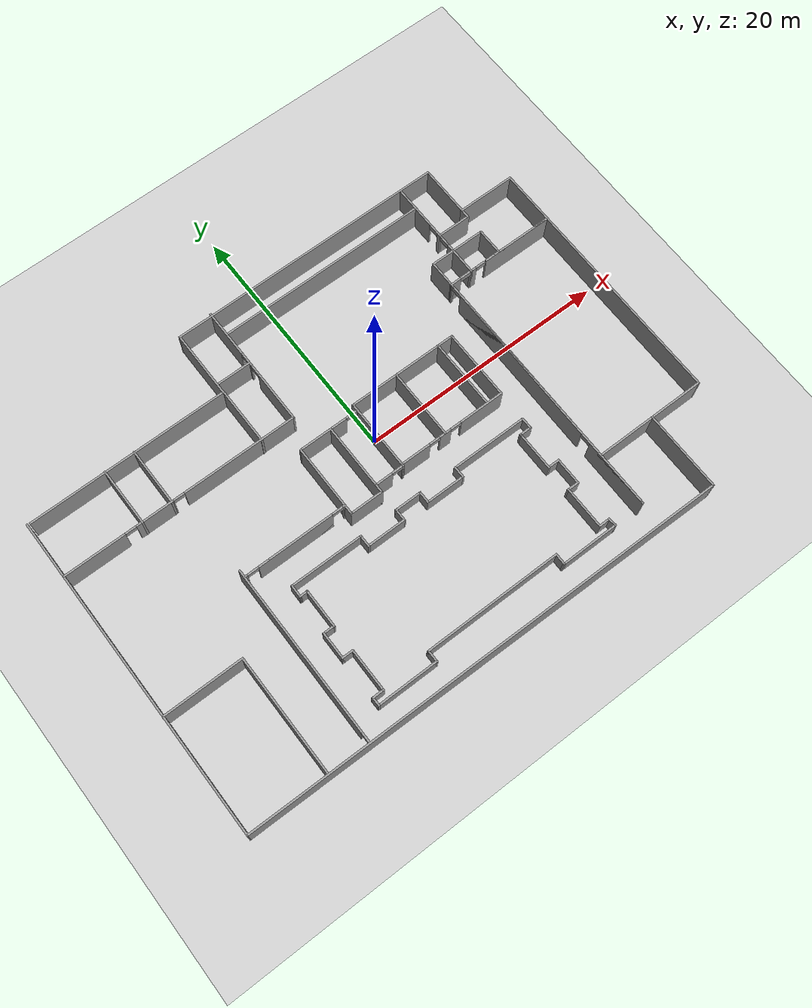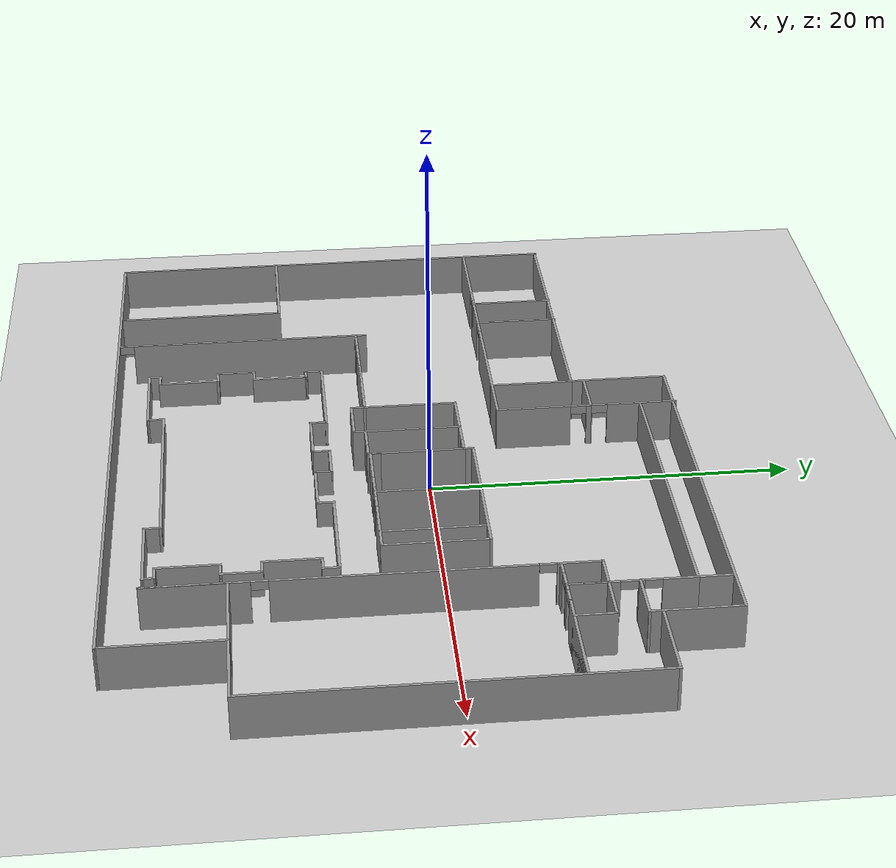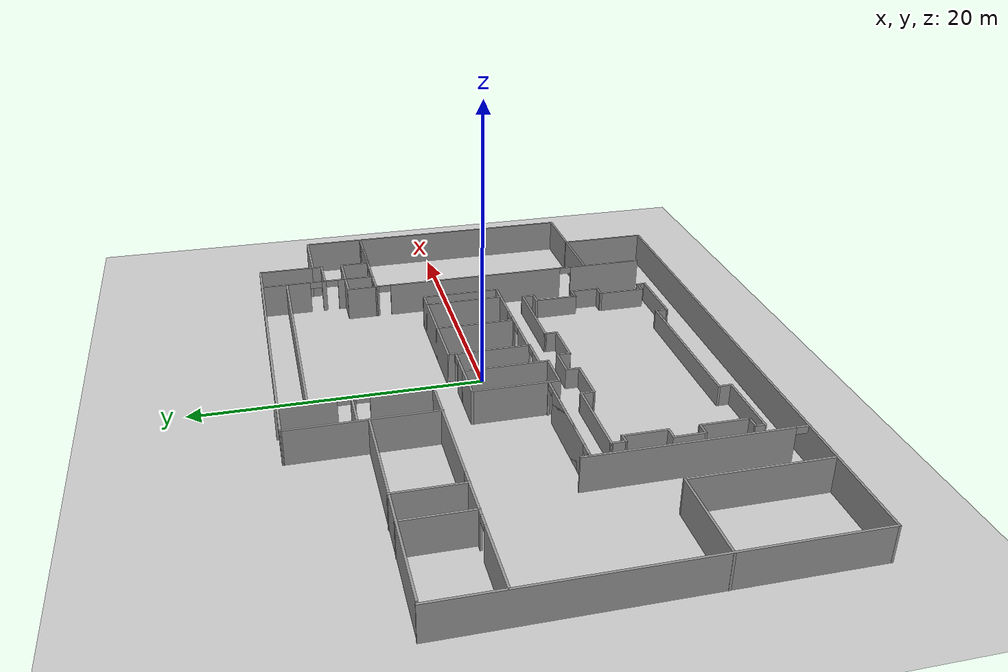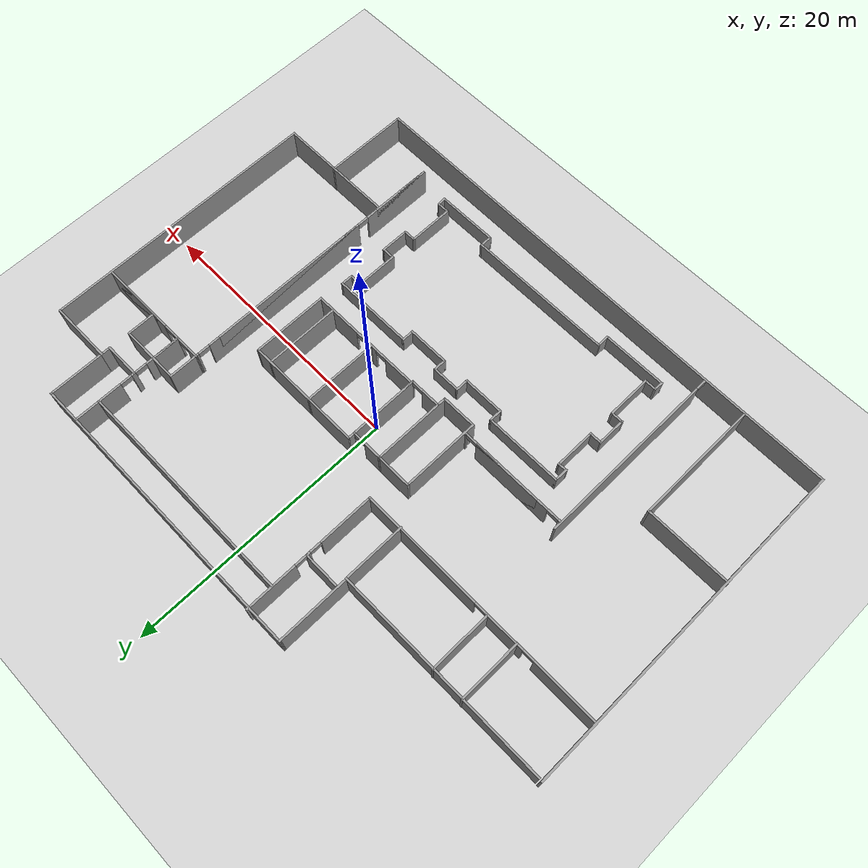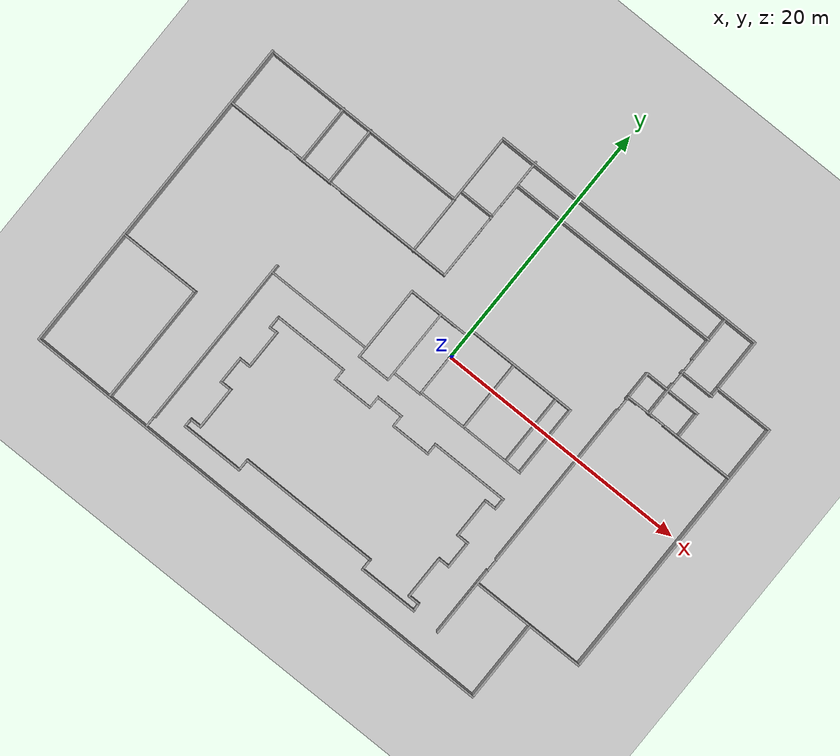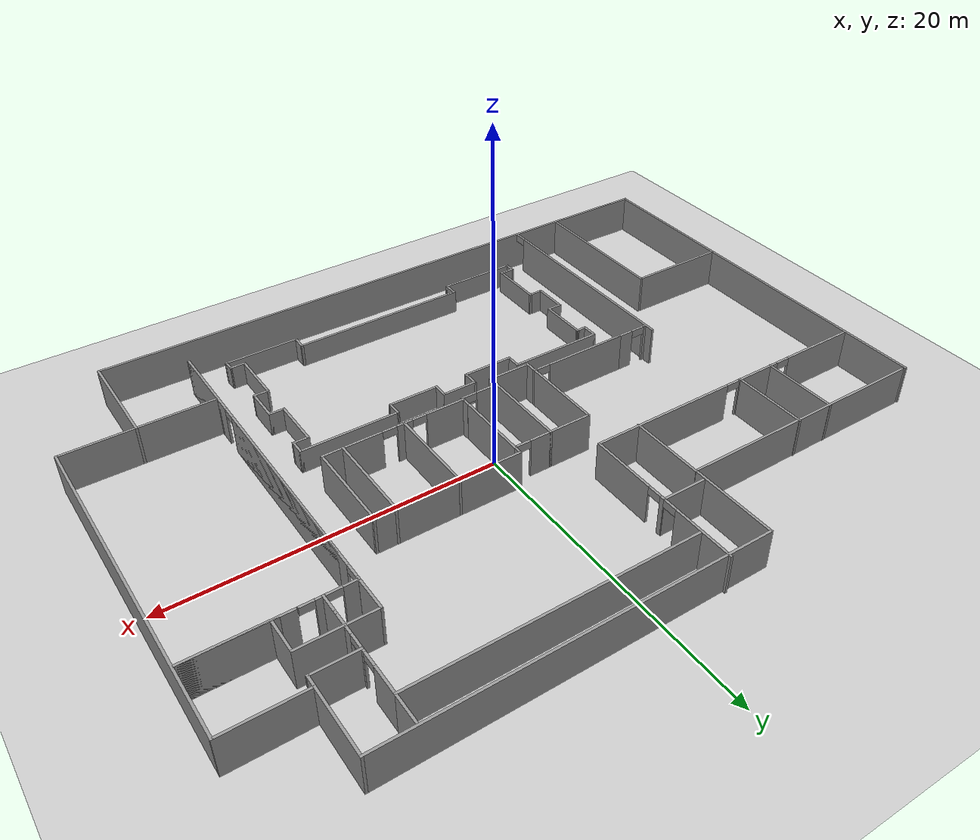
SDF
<sdf version="1.6">
 <world name="default">
  <light name="sun" type="directional">
   <pose>0 0 10 0 -0 0</pose>
   <diffuse>0.8 0.8 0.8 1</diffuse>
   <specular>0.1 0.1 0.1 1</specular>
   <attenuation>
    <range>1000</range>
    <constant>0.9</constant>
    <linear>0.01</linear>
    <quadratic>0.001</quadratic>
   </attenuation>
   <direction>-0.5 0.5 -1</direction>
  </light>
  <model name="ground_plane">
   <static>1</static>
   <link name="link">
    <collision name="collision">
     <geometry><plane><normal>0 0 1</normal><size>100 100</size></plane></geometry>
     <surface><friction><ode><mu>100</mu><mu2>50</mu2></ode></friction></surface>
    </collision>
    <visual name="visual">
     <cast_shadows>0</cast_shadows>
     <geometry><plane><normal>0 0 1</normal><size>100 100</size></plane></geometry>
     <material>
      <script><uri>file://media/materials/scripts/gazebo.material</uri><name>Gazebo/Grey</name></script>
     </material>
    </visual>
   </link>
  </model>
  <gravity>0 0 -9.8</gravity>
  <magnetic_field>6e-06 2.3e-05 -4.2e-05</magnetic_field>
  <atmosphere type="adiabatic"/>
  <physics name="default_physics" default="0" type="ode">
   <max_step_size>0.001</max_step_size>
   <real_time_factor>1</real_time_factor>
   <real_time_update_rate>1000</real_time_update_rate>
  </physics>
  <scene><ambient>0.4 0.4 0.4 1</ambient><background>0.7 0.7 0.7 1</background><shadows>1</shadows></scene>
  <spherical_coordinates>
   <surface_model>EARTH_WGS84</surface_model>
   <latitude_deg>0</latitude_deg>
   <longitude_deg>0</longitude_deg>
   <elevation>0</elevation>
   <heading_deg>0</heading_deg>
  </spherical_coordinates>
  <model name="REPF">
   <pose>-1.32849 -1.57577 0 0 -0 0</pose>
   <link name="Wall_291">
    <collision name="Wall_291_Collision">
     <geometry><box><size>26 0.15 2.5</size></box></geometry>
     <pose>0 0 1.25 0 -0 0</pose>
    </collision>
    <visual name="Wall_291_Visual">
     <pose>0 0 1.25 0 -0 0</pose>
     <geometry><box><size>26 0.15 2.5</size></box></geometry>
     <material>
      <script><uri>file://media/materials/scripts/gazebo.material</uri><name>Gazebo/Grey</name></script>
      <ambient>1 1 1 1</ambient>
     </material>
    </visual>
    <pose>-21.7531 -2.59206 0 0 0 -1.5708</pose>
   </link>
   <link name="Wall_292">
    <collision name="Wall_292_Collision">
     <geometry><box><size>39.3304 0.15 2.5</size></box></geometry>
     <pose>0 0 1.25 0 -0 0</pose>
    </collision>
    <visual name="Wall_292_Visual">
     <pose>0 0 1.25 0 -0 0</pose>
     <geometry><box><size>39.3304 0.15 2.5</size></box></geometry>
     <material>
      <script><uri>file://media/materials/scripts/gazebo.material</uri><name>Gazebo/Grey</name></script>
      <ambient>1 1 1 1</ambient>
     </material>
    </visual>
    <pose>-2.16853 -15.6825 0 0 0 -0.008444</pose>
   </link>
   <link name="Wall_293">
    <collision name="Wall_293_Collision">
     <geometry><box><size>6.5 0.15 2.5</size></box></geometry>
     <pose>0 0 1.25 0 -0 0</pose>
    </collision>
    <visual name="Wall_293_Visual">
     <pose>0 0 1.25 0 -0 0</pose>
     <geometry><box><size>6.5 0.15 2.5</size></box></geometry>
     <material>
      <script><uri>file://media/materials/scripts/gazebo.material</uri><name>Gazebo/Grey</name></script>
      <ambient>1 1 1 1</ambient>
     </material>
    </visual>
    <pose>17.421 -12.6729 0 0 -0 1.5708</pose>
   </link>
   <link name="Wall_294">
    <collision name="Wall_294_Collision">
     <geometry><box><size>4.5 0.15 2.5</size></box></geometry>
     <pose>0 0 1.25 0 -0 0</pose>
    </collision>
    <visual name="Wall_294_Visual">
     <pose>0 0 1.25 0 -0 0</pose>
     <geometry><box><size>4.5 0.15 2.5</size></box></geometry>
     <material>
      <script><uri>file://media/materials/scripts/gazebo.material</uri><name>Gazebo/Grey</name></script>
      <ambient>1 1 1 1</ambient>
     </material>
    </visual>
    <pose>19.596 -9.49791 0 0 -0 0</pose>
   </link>
   <link name="Wall_295">
    <collision name="Wall_295_Collision">
     <geometry><box><size>21.25 0.15 2.5</size></box></geometry>
     <pose>0 0 1.25 0 -0 0</pose>
    </collision>
    <visual name="Wall_295_Visual">
     <pose>0 0 1.25 0 -0 0</pose>
     <geometry><box><size>21.25 0.15 2.5</size></box></geometry>
     <material>
      <script><uri>file://media/materials/scripts/gazebo.material</uri><name>Gazebo/Grey</name></script>
      <ambient>1 1 1 1</ambient>
     </material>
    </visual>
    <pose>21.771 1.05209 0 0 -0 1.5708</pose>
   </link>
   <link name="Wall_296">
    <collision name="Wall_296_Collision">
     <geometry><box><size>4.75 0.15 2.5</size></box></geometry>
     <pose>0 0 1.25 0 -0 0</pose>
    </collision>
    <visual name="Wall_296_Visual">
     <pose>0 0 1.25 0 -0 0</pose>
     <geometry><box><size>4.75 0.15 2.5</size></box></geometry>
     <material>
      <script><uri>file://media/materials/scripts/gazebo.material</uri><name>Gazebo/Grey</name></script>
      <ambient>1 1 1 1</ambient>
     </material>
    </visual>
    <pose>19.471 11.6021 0 0 -0 3.14159</pose>
   </link>
   <link name="Wall_297">
    <collision name="Wall_297_Collision">
     <geometry><box><size>4.25 0.15 2.5</size></box></geometry>
     <pose>0 0 1.25 0 -0 0</pose>
    </collision>
    <visual name="Wall_297_Visual">
     <pose>0 0 1.25 0 -0 0</pose>
     <geometry><box><size>4.25 0.15 2.5</size></box></geometry>
     <material>
      <script><uri>file://media/materials/scripts/gazebo.material</uri><name>Gazebo/Grey</name></script>
      <ambient>1 1 1 1</ambient>
     </material>
    </visual>
    <pose>17.171 13.6521 0 0 -0 1.5708</pose>
   </link>
   <link name="Wall_298">
    <collision name="Wall_298_Collision">
     <geometry><box><size>22.75 0.15 2.5</size></box></geometry>
     <pose>0 0 1.25 0 -0 0</pose>
    </collision>
    <visual name="Wall_298_Visual">
     <pose>0 0 1.25 0 -0 0</pose>
     <geometry><box><size>22.75 0.15 2.5</size></box></geometry>
     <material>
      <script><uri>file://media/materials/scripts/gazebo.material</uri><name>Gazebo/Grey</name></script>
      <ambient>1 1 1 1</ambient>
     </material>
    </visual>
    <pose>5.87097 15.7021 0 0 -0 3.14159</pose>
   </link>
   <link name="Wall_299">
    <collision name="Wall_299_Collision">
     <geometry><box><size>5.55237 0.15 2.5</size></box></geometry>
     <pose>0 0 1.25 0 -0 0</pose>
    </collision>
    <visual name="Wall_299_Visual">
     <pose>0 0 1.25 0 -0 0</pose>
     <geometry><box><size>5.55237 0.15 2.5</size></box></geometry>
     <material>
      <script><uri>file://media/materials/scripts/gazebo.material</uri><name>Gazebo/Grey</name></script>
      <ambient>1 1 1 1</ambient>
     </material>
    </visual>
    <pose>-5.42804 13.0009 0 0 0 -1.57043</pose>
   </link>
   <link name="Wall_300">
    <collision name="Wall_300_Collision">
     <geometry><box><size>16.25 0.15 2.5</size></box></geometry>
     <pose>0 0 1.25 0 -0 0</pose>
    </collision>
    <visual name="Wall_300_Visual">
     <pose>0 0 1.25 0 -0 0</pose>
     <geometry><box><size>16.25 0.15 2.5</size></box></geometry>
     <material>
      <script><uri>file://media/materials/scripts/gazebo.material</uri><name>Gazebo/Grey</name></script>
      <ambient>1 1 1 1</ambient>
     </material>
    </visual>
    <pose>-13.4469 10.2997 0 0 -0 3.14159</pose>
   </link>
   <link name="Wall_302">
    <pose>-2.62455 10.7985 0 0 0 -1.5708</pose>
    <visual name="Wall_302_Visual_0">
     <pose>-3.14213 0 1.25 0 -0 0</pose>
     <geometry><box><size>3.96575 0.15 2.5</size></box></geometry>
     <material>
      <script><uri>file://media/materials/scripts/gazebo.material</uri><name>Gazebo/Grey</name></script>
      <ambient>1 1 1 1</ambient>
     </material>
    </visual>
    <collision name="Wall_302_Collision_0">
     <geometry><box><size>3.96575 0.15 2.5</size></box></geometry>
     <pose>-3.14213 0 1.25 0 -0 0</pose>
    </collision>
    <visual name="Wall_302_Visual_1">
     <pose>-0.118157 0 1.25 0 -0 0</pose>
     <geometry><box><size>0.282192 0.15 2.5</size></box></geometry>
     <material>
      <script><uri>file://media/materials/scripts/gazebo.material</uri><name>Gazebo/Grey</name></script>
      <ambient>1 1 1 1</ambient>
     </material>
    </visual>
    <collision name="Wall_302_Collision_1">
     <geometry><box><size>0.282192 0.15 2.5</size></box></geometry>
     <pose>-0.118157 0 1.25 0 -0 0</pose>
    </collision>
    <visual name="Wall_302_Visual_2">
     <pose>3.02397 0 1.25 0 -0 0</pose>
     <geometry><box><size>4.20206 0.15 2.5</size></box></geometry>
     <material>
      <script><uri>file://media/materials/scripts/gazebo.material</uri><name>Gazebo/Grey</name></script>
      <ambient>1 1 1 1</ambient>
     </material>
    </visual>
    <collision name="Wall_302_Collision_2">
     <geometry><box><size>4.20206 0.15 2.5</size></box></geometry>
     <pose>3.02397 0 1.25 0 -0 0</pose>
    </collision>
    <visual name="Wall_302_Visual_3">
     <pose>-0.709253 0 2.25 0 -0 0</pose>
     <geometry><box><size>0.9 0.15 0.5</size></box></geometry>
     <material>
      <script><uri>file://media/materials/scripts/gazebo.material</uri><name>Gazebo/Grey</name></script>
      <ambient>1 1 1 1</ambient>
     </material>
    </visual>
    <collision name="Wall_302_Collision_3">
     <geometry><box><size>0.9 0.15 0.5</size></box></geometry>
     <pose>-0.709253 0 2.25 0 -0 0</pose>
    </collision>
    <visual name="Wall_302_Visual_4">
     <pose>0.472939 0 2.25 0 -0 0</pose>
     <geometry><box><size>0.9 0.15 0.5</size></box></geometry>
     <material>
      <script><uri>file://media/materials/scripts/gazebo.material</uri><name>Gazebo/Grey</name></script>
      <ambient>1 1 1 1</ambient>
     </material>
    </visual>
    <collision name="Wall_302_Collision_4">
     <geometry><box><size>0.9 0.15 0.5</size></box></geometry>
     <pose>0.472939 0 2.25 0 -0 0</pose>
    </collision>
   </link>
   <link name="Wall_303">
    <pose>-12.1746 5.74854 0 0 -0 3.14159</pose>
    <visual name="Wall_303_Visual_0">
     <pose>-4.94527 0 1.25 0 -0 0</pose>
     <geometry><box><size>9.35946 0.15 2.5</size></box></geometry>
     <material>
      <script><uri>file://media/materials/scripts/gazebo.material</uri><name>Gazebo/Grey</name></script>
      <ambient>1 1 1 1</ambient>
     </material>
    </visual>
    <collision name="Wall_303_Collision_0">
     <geometry><box><size>9.35946 0.15 2.5</size></box></geometry>
     <pose>-4.94527 0 1.25 0 -0 0</pose>
    </collision>
    <visual name="Wall_303_Visual_1">
     <pose>2.17509 0 1.25 0 -0 0</pose>
     <geometry><box><size>3.08126 0.15 2.5</size></box></geometry>
     <material>
      <script><uri>file://media/materials/scripts/gazebo.material</uri><name>Gazebo/Grey</name></script>
      <ambient>1 1 1 1</ambient>
     </material>
    </visual>
    <collision name="Wall_303_Collision_1">
     <geometry><box><size>3.08126 0.15 2.5</size></box></geometry>
     <pose>2.17509 0 1.25 0 -0 0</pose>
    </collision>
    <visual name="Wall_303_Visual_2">
     <pose>7.12036 0 1.25 0 -0 0</pose>
     <geometry><box><size>5.00928 0.15 2.5</size></box></geometry>
     <material>
      <script><uri>file://media/materials/scripts/gazebo.material</uri><name>Gazebo/Grey</name></script>
      <ambient>1 1 1 1</ambient>
     </material>
    </visual>
    <collision name="Wall_303_Collision_2">
     <geometry><box><size>5.00928 0.15 2.5</size></box></geometry>
     <pose>7.12036 0 1.25 0 -0 0</pose>
    </collision>
    <visual name="Wall_303_Visual_3">
     <pose>0.18446 0 2.25 0 -0 0</pose>
     <geometry><box><size>0.9 0.15 0.5</size></box></geometry>
     <material>
      <script><uri>file://media/materials/scripts/gazebo.material</uri><name>Gazebo/Grey</name></script>
      <ambient>1 1 1 1</ambient>
     </material>
    </visual>
    <collision name="Wall_303_Collision_3">
     <geometry><box><size>0.9 0.15 0.5</size></box></geometry>
     <pose>0.18446 0 2.25 0 -0 0</pose>
    </collision>
    <visual name="Wall_303_Visual_4">
     <pose>4.16572 0 2.25 0 -0 0</pose>
     <geometry><box><size>0.9 0.15 0.5</size></box></geometry>
     <material>
      <script><uri>file://media/materials/scripts/gazebo.material</uri><name>Gazebo/Grey</name></script>
      <ambient>1 1 1 1</ambient>
     </material>
    </visual>
    <collision name="Wall_303_Collision_4">
     <geometry><box><size>0.9 0.15 0.5</size></box></geometry>
     <pose>4.16572 0 2.25 0 -0 0</pose>
    </collision>
   </link>
   <link name="Wall_305">
    <collision name="Wall_305_Collision">
     <geometry><box><size>4.75 0.15 2.5</size></box></geometry>
     <pose>0 0 1.25 0 -0 0</pose>
    </collision>
    <visual name="Wall_305_Visual">
     <pose>0 0 1.25 0 -0 0</pose>
     <geometry><box><size>4.75 0.15 2.5</size></box></geometry>
     <material>
      <script><uri>file://media/materials/scripts/gazebo.material</uri><name>Gazebo/Grey</name></script>
      <ambient>1 1 1 1</ambient>
     </material>
    </visual>
    <pose>-5.39685 7.99971 0 0 0 -1.5708</pose>
   </link>
   <link name="Wall_307">
    <collision name="Wall_307_Collision">
     <geometry><box><size>2.75 0.15 2.5</size></box></geometry>
     <pose>0 0 1.25 0 -0 0</pose>
    </collision>
    <visual name="Wall_307_Visual">
     <pose>0 0 1.25 0 -0 0</pose>
     <geometry><box><size>2.75 0.15 2.5</size></box></geometry>
     <material>
      <script><uri>file://media/materials/scripts/gazebo.material</uri><name>Gazebo/Grey</name></script>
      <ambient>1 1 1 1</ambient>
     </material>
    </visual>
    <pose>-3.94634 11.0349 0 0 -0 0</pose>
   </link>
   <link name="Wall_309">
    <collision name="Wall_309_Collision">
     <geometry><box><size>17.25 0.15 2.5</size></box></geometry>
     <pose>0 0 1.25 0 -0 0</pose>
    </collision>
    <visual name="Wall_309_Visual">
     <pose>0 0 1.25 0 -0 0</pose>
     <geometry><box><size>17.25 0.15 2.5</size></box></geometry>
     <material>
      <script><uri>file://media/materials/scripts/gazebo.material</uri><name>Gazebo/Grey</name></script>
      <ambient>1 1 1 1</ambient>
     </material>
    </visual>
    <pose>5.99398 13.832 0 0 -0 0</pose>
   </link>
   <link name="Wall_310">
    <collision name="Wall_310_Collision">
     <geometry><box><size>2 0.15 2.5</size></box></geometry>
     <pose>0 0 1.25 0 -0 0</pose>
    </collision>
    <visual name="Wall_310_Visual">
     <pose>0 0 1.25 0 -0 0</pose>
     <geometry><box><size>2 0.15 2.5</size></box></geometry>
     <material>
      <script><uri>file://media/materials/scripts/gazebo.material</uri><name>Gazebo/Grey</name></script>
      <ambient>1 1 1 1</ambient>
     </material>
    </visual>
    <pose>14.544 14.757 0 0 -0 1.5708</pose>
   </link>
   <link name="Wall_312">
    <pose>14.544 10.532 0 0 0 -1.5708</pose>
    <visual name="Wall_312_Visual_0">
     <pose>-2.44988 0 1.25 0 -0 0</pose>
     <geometry><box><size>1.85025 0.15 2.5</size></box></geometry>
     <material>
      <script><uri>file://media/materials/scripts/gazebo.material</uri><name>Gazebo/Grey</name></script>
      <ambient>1 1 1 1</ambient>
     </material>
    </visual>
    <collision name="Wall_312_Collision_0">
     <geometry><box><size>1.85025 0.15 2.5</size></box></geometry>
     <pose>-2.44988 0 1.25 0 -0 0</pose>
    </collision>
    <visual name="Wall_312_Visual_1">
     <pose>-0.462424 0 1.25 0 -0 0</pose>
     <geometry><box><size>0.324652 0.15 2.5</size></box></geometry>
     <material>
      <script><uri>file://media/materials/scripts/gazebo.material</uri><name>Gazebo/Grey</name></script>
      <ambient>1 1 1 1</ambient>
     </material>
    </visual>
    <collision name="Wall_312_Collision_1">
     <geometry><box><size>0.324652 0.15 2.5</size></box></geometry>
     <pose>-0.462424 0 1.25 0 -0 0</pose>
    </collision>
    <visual name="Wall_312_Visual_2">
     <pose>1.98745 0 1.25 0 -0 0</pose>
     <geometry><box><size>2.7751 0.15 2.5</size></box></geometry>
     <material>
      <script><uri>file://media/materials/scripts/gazebo.material</uri><name>Gazebo/Grey</name></script>
      <ambient>1 1 1 1</ambient>
     </material>
    </visual>
    <collision name="Wall_312_Collision_2">
     <geometry><box><size>2.7751 0.15 2.5</size></box></geometry>
     <pose>1.98745 0 1.25 0 -0 0</pose>
    </collision>
    <visual name="Wall_312_Visual_3">
     <pose>-1.07475 0 2.25 0 -0 0</pose>
     <geometry><box><size>0.9 0.15 0.5</size></box></geometry>
     <material>
      <script><uri>file://media/materials/scripts/gazebo.material</uri><name>Gazebo/Grey</name></script>
      <ambient>1 1 1 1</ambient>
     </material>
    </visual>
    <collision name="Wall_312_Collision_3">
     <geometry><box><size>0.9 0.15 0.5</size></box></geometry>
     <pose>-1.07475 0 2.25 0 -0 0</pose>
    </collision>
    <visual name="Wall_312_Visual_4">
     <pose>0.149902 0 2.25 0 -0 0</pose>
     <geometry><box><size>0.9 0.15 0.5</size></box></geometry>
     <material>
      <script><uri>file://media/materials/scripts/gazebo.material</uri><name>Gazebo/Grey</name></script>
      <ambient>1 1 1 1</ambient>
     </material>
    </visual>
    <collision name="Wall_312_Collision_4">
     <geometry><box><size>0.9 0.15 0.5</size></box></geometry>
     <pose>0.149902 0 2.25 0 -0 0</pose>
    </collision>
   </link>
   <link name="Wall_313">
    <pose>13.619 7.22222 0 0 0 -3.13104</pose>
    <visual name="Wall_313_Visual_0">
     <pose>-0.91553 0 1.25 0 -0 0</pose>
     <geometry><box><size>0.168939 0.15 2.5</size></box></geometry>
     <material>
      <script><uri>file://media/materials/scripts/gazebo.material</uri><name>Gazebo/Grey</name></script>
      <ambient>1 1 1 1</ambient>
     </material>
    </visual>
    <collision name="Wall_313_Collision_0">
     <geometry><box><size>0.168939 0.15 2.5</size></box></geometry>
     <pose>-0.91553 0 1.25 0 -0 0</pose>
    </collision>
    <visual name="Wall_313_Visual_1">
     <pose>0.53447 0 1.25 0 -0 0</pose>
     <geometry><box><size>0.931061 0.15 2.5</size></box></geometry>
     <material>
      <script><uri>file://media/materials/scripts/gazebo.material</uri><name>Gazebo/Grey</name></script>
      <ambient>1 1 1 1</ambient>
     </material>
    </visual>
    <collision name="Wall_313_Collision_1">
     <geometry><box><size>0.931061 0.15 2.5</size></box></geometry>
     <pose>0.53447 0 1.25 0 -0 0</pose>
    </collision>
    <visual name="Wall_313_Visual_2">
     <pose>-0.381061 0 2.25 0 -0 0</pose>
     <geometry><box><size>0.9 0.15 0.5</size></box></geometry>
     <material>
      <script><uri>file://media/materials/scripts/gazebo.material</uri><name>Gazebo/Grey</name></script>
      <ambient>1 1 1 1</ambient>
     </material>
    </visual>
    <collision name="Wall_313_Collision_2">
     <geometry><box><size>0.9 0.15 0.5</size></box></geometry>
     <pose>-0.381061 0 2.25 0 -0 0</pose>
    </collision>
   </link>
   <link name="Wall_314">
    <collision name="Wall_314_Collision">
     <geometry><box><size>2.26953 0.15 2.5</size></box></geometry>
     <pose>0 0 1.25 0 -0 0</pose>
    </collision>
    <visual name="Wall_314_Visual">
     <pose>0 0 1.25 0 -0 0</pose>
     <geometry><box><size>2.26953 0.15 2.5</size></box></geometry>
     <material>
      <script><uri>file://media/materials/scripts/gazebo.material</uri><name>Gazebo/Grey</name></script>
      <ambient>1 1 1 1</ambient>
     </material>
    </visual>
    <pose>12.694 8.27222 0 0 -0 1.5708</pose>
   </link>
   <link name="Wall_315">
    <collision name="Wall_315_Collision">
     <geometry><box><size>2 0.15 2.5</size></box></geometry>
     <pose>0 0 1.25 0 -0 0</pose>
    </collision>
    <visual name="Wall_315_Visual">
     <pose>0 0 1.25 0 -0 0</pose>
     <geometry><box><size>2 0.15 2.5</size></box></geometry>
     <material>
      <script><uri>file://media/materials/scripts/gazebo.material</uri><name>Gazebo/Grey</name></script>
      <ambient>1 1 1 1</ambient>
     </material>
    </visual>
    <pose>13.619 9.33198 0 0 -0 0</pose>
   </link>
   <link name="Wall_317">
    <collision name="Wall_317_Collision">
     <geometry><box><size>2.75 0.15 2.5</size></box></geometry>
     <pose>0 0 1.25 0 -0 0</pose>
    </collision>
    <visual name="Wall_317_Visual">
     <pose>0 0 1.25 0 -0 0</pose>
     <geometry><box><size>2.75 0.15 2.5</size></box></geometry>
     <material>
      <script><uri>file://media/materials/scripts/gazebo.material</uri><name>Gazebo/Grey</name></script>
      <ambient>1 1 1 1</ambient>
     </material>
    </visual>
    <pose>15.8713 10.9244 0 0 -0 0</pose>
   </link>
   <link name="Wall_318">
    <collision name="Wall_318_Collision">
     <geometry><box><size>0.827663 0.15 2.5</size></box></geometry>
     <pose>0 0 1.25 0 -0 0</pose>
    </collision>
    <visual name="Wall_318_Visual">
     <pose>0 0 1.25 0 -0 0</pose>
     <geometry><box><size>0.827663 0.15 2.5</size></box></geometry>
     <material>
      <script><uri>file://media/materials/scripts/gazebo.material</uri><name>Gazebo/Grey</name></script>
      <ambient>1 1 1 1</ambient>
     </material>
    </visual>
    <pose>17.1711 11.2633 0 0 -0 1.57131</pose>
   </link>
   <link name="Wall_320">
    <collision name="Wall_320_Collision">
     <geometry><box><size>2.25 0.15 2.5</size></box></geometry>
     <pose>0 0 1.25 0 -0 0</pose>
    </collision>
    <visual name="Wall_320_Visual">
     <pose>0 0 1.25 0 -0 0</pose>
     <geometry><box><size>2.25 0.15 2.5</size></box></geometry>
     <material>
      <script><uri>file://media/materials/scripts/gazebo.material</uri><name>Gazebo/Grey</name></script>
      <ambient>1 1 1 1</ambient>
     </material>
    </visual>
    <pose>14.544 8.28198 0 0 0 -1.5708</pose>
   </link>
   <link name="Wall_321">
    <pose>18.094 7.23198 0 0 -0 0</pose>
    <visual name="Wall_321_Visual_0">
     <pose>-3.36352 0 1.25 0 -0 0</pose>
     <geometry><box><size>0.522969 0.15 2.5</size></box></geometry>
     <material>
      <script><uri>file://media/materials/scripts/gazebo.material</uri><name>Gazebo/Grey</name></script>
      <ambient>1 1 1 1</ambient>
     </material>
    </visual>
    <collision name="Wall_321_Collision_0">
     <geometry><box><size>0.522969 0.15 2.5</size></box></geometry>
     <pose>-3.36352 0 1.25 0 -0 0</pose>
    </collision>
    <visual name="Wall_321_Visual_1">
     <pose>0.711485 0 1.25 0 -0 0</pose>
     <geometry><box><size>5.82703 0.15 2.5</size></box></geometry>
     <material>
      <script><uri>file://media/materials/scripts/gazebo.material</uri><name>Gazebo/Grey</name></script>
      <ambient>1 1 1 1</ambient>
     </material>
    </visual>
    <collision name="Wall_321_Collision_1">
     <geometry><box><size>5.82703 0.15 2.5</size></box></geometry>
     <pose>0.711485 0 1.25 0 -0 0</pose>
    </collision>
    <visual name="Wall_321_Visual_2">
     <pose>1.13616 0 1.25 0 -0 0</pose>
     <geometry><box><size>4.97768 0.15 2.5</size></box></geometry>
     <material>
      <script><uri>file://media/materials/scripts/gazebo.material</uri><name>Gazebo/Grey</name></script>
      <ambient>1 1 1 1</ambient>
     </material>
    </visual>
    <collision name="Wall_321_Collision_2">
     <geometry><box><size>4.97768 0.15 2.5</size></box></geometry>
     <pose>1.13616 0 1.25 0 -0 0</pose>
    </collision>
    <visual name="Wall_321_Visual_3">
     <pose>-2.67735 0 2.25 0 -0 0</pose>
     <geometry><box><size>0.849354 0.15 0.5</size></box></geometry>
     <material>
      <script><uri>file://media/materials/scripts/gazebo.material</uri><name>Gazebo/Grey</name></script>
      <ambient>1 1 1 1</ambient>
     </material>
    </visual>
    <collision name="Wall_321_Collision_3">
     <geometry><box><size>0.849354 0.15 0.5</size></box></geometry>
     <pose>-2.67735 0 2.25 0 -0 0</pose>
    </collision>
   </link>
   <link name="Wall_323">
    <collision name="Wall_323_Collision">
     <geometry><box><size>2.75 0.15 2.5</size></box></geometry>
     <pose>0 0 1.25 0 -0 0</pose>
    </collision>
    <visual name="Wall_323_Visual">
     <pose>0 0 1.25 0 -0 0</pose>
     <geometry><box><size>2.75 0.15 2.5</size></box></geometry>
     <material>
      <script><uri>file://media/materials/scripts/gazebo.material</uri><name>Gazebo/Grey</name></script>
      <ambient>1 1 1 1</ambient>
     </material>
    </visual>
    <pose>15.844 9.33198 0 0 -0 0</pose>
   </link>
   <link name="Wall_324">
    <collision name="Wall_324_Collision">
     <geometry><box><size>2.25 0.15 2.5</size></box></geometry>
     <pose>0 0 1.25 0 -0 0</pose>
    </collision>
    <visual name="Wall_324_Visual">
     <pose>0 0 1.25 0 -0 0</pose>
     <geometry><box><size>2.25 0.15 2.5</size></box></geometry>
     <material>
      <script><uri>file://media/materials/scripts/gazebo.material</uri><name>Gazebo/Grey</name></script>
      <ambient>1 1 1 1</ambient>
     </material>
    </visual>
    <pose>17.144 8.28198 0 0 0 -1.5708</pose>
   </link>
   <link name="Wall_327">
    <pose>12.694 -3.32778 0 0 0 -1.5708</pose>
    <visual name="Wall_327_Visual_0">
     <pose>-10.4755 0 1.25 0 -0 0</pose>
     <geometry><box><size>0.29897 0.15 2.5</size></box></geometry>
     <material>
      <script><uri>file://media/materials/scripts/gazebo.material</uri><name>Gazebo/Grey</name></script>
      <ambient>1 1 1 1</ambient>
     </material>
    </visual>
    <collision name="Wall_327_Collision_0">
     <geometry><box><size>0.29897 0.15 2.5</size></box></geometry>
     <pose>-10.4755 0 1.25 0 -0 0</pose>
    </collision>
    <visual name="Wall_327_Visual_1">
     <pose>-2.64993 0 1.25 0 -0 0</pose>
     <geometry><box><size>13.5522 0.15 2.5</size></box></geometry>
     <material>
      <script><uri>file://media/materials/scripts/gazebo.material</uri><name>Gazebo/Grey</name></script>
      <ambient>1 1 1 1</ambient>
     </material>
    </visual>
    <collision name="Wall_327_Collision_1">
     <geometry><box><size>13.5522 0.15 2.5</size></box></geometry>
     <pose>-2.64993 0 1.25 0 -0 0</pose>
    </collision>
    <visual name="Wall_327_Visual_2">
     <pose>-2.20373 0 1.25 0 -0 0</pose>
     <geometry><box><size>12.6598 0.15 2.5</size></box></geometry>
     <material>
      <script><uri>file://media/materials/scripts/gazebo.material</uri><name>Gazebo/Grey</name></script>
      <ambient>1 1 1 1</ambient>
     </material>
    </visual>
    <collision name="Wall_327_Collision_2">
     <geometry><box><size>12.6598 0.15 2.5</size></box></geometry>
     <pose>-2.20373 0 1.25 0 -0 0</pose>
    </collision>
    <visual name="Wall_327_Visual_3">
     <pose>7.82559 0 1.25 0 -0 0</pose>
     <geometry><box><size>5.59883 0.15 2.5</size></box></geometry>
     <material>
      <script><uri>file://media/materials/scripts/gazebo.material</uri><name>Gazebo/Grey</name></script>
      <ambient>1 1 1 1</ambient>
     </material>
    </visual>
    <collision name="Wall_327_Collision_3">
     <geometry><box><size>5.59883 0.15 2.5</size></box></geometry>
     <pose>7.82559 0 1.25 0 -0 0</pose>
    </collision>
    <visual name="Wall_327_Visual_4">
     <pose>8.27478 0 1.25 0 -0 0</pose>
     <geometry><box><size>4.70045 0.15 2.5</size></box></geometry>
     <material>
      <script><uri>file://media/materials/scripts/gazebo.material</uri><name>Gazebo/Grey</name></script>
      <ambient>1 1 1 1</ambient>
     </material>
    </visual>
    <collision name="Wall_327_Collision_4">
     <geometry><box><size>4.70045 0.15 2.5</size></box></geometry>
     <pose>8.27478 0 1.25 0 -0 0</pose>
    </collision>
    <visual name="Wall_327_Visual_5">
     <pose>-9.87983 0 2.25 0 -0 0</pose>
     <geometry><box><size>0.892405 0.15 0.5</size></box></geometry>
     <material>
      <script><uri>file://media/materials/scripts/gazebo.material</uri><name>Gazebo/Grey</name></script>
      <ambient>1 1 1 1</ambient>
     </material>
    </visual>
    <collision name="Wall_327_Collision_5">
     <geometry><box><size>0.892405 0.15 0.5</size></box></geometry>
     <pose>-9.87983 0 2.25 0 -0 0</pose>
    </collision>
    <visual name="Wall_327_Visual_6">
     <pose>4.57536 0 2.25 0 -0 0</pose>
     <geometry><box><size>0.89838 0.15 0.5</size></box></geometry>
     <material>
      <script><uri>file://media/materials/scripts/gazebo.material</uri><name>Gazebo/Grey</name></script>
      <ambient>1 1 1 1</ambient>
     </material>
    </visual>
    <collision name="Wall_327_Collision_6">
     <geometry><box><size>0.89838 0.15 0.5</size></box></geometry>
     <pose>4.57536 0 2.25 0 -0 0</pose>
    </collision>
    <visual name="Wall_327_Visual_7">
     <pose>4.57536 0 2.25 0 -0 0</pose>
     <geometry><box><size>0.89838 0.15 0.5</size></box></geometry>
     <material>
      <script><uri>file://media/materials/scripts/gazebo.material</uri><name>Gazebo/Grey</name></script>
      <ambient>1 1 1 1</ambient>
     </material>
    </visual>
    <collision name="Wall_327_Collision_7">
     <geometry><box><size>0.89838 0.15 0.5</size></box></geometry>
     <pose>4.57536 0 2.25 0 -0 0</pose>
    </collision>
   </link>
   <link name="Wall_329">
    <collision name="Wall_329_Collision">
     <geometry><box><size>4.75 0.15 2.5</size></box></geometry>
     <pose>0 0 1.25 0 -0 0</pose>
    </collision>
    <visual name="Wall_329_Visual">
     <pose>0 0 1.25 0 -0 0</pose>
     <geometry><box><size>4.75 0.15 2.5</size></box></geometry>
     <material>
      <script><uri>file://media/materials/scripts/gazebo.material</uri><name>Gazebo/Grey</name></script>
      <ambient>1 1 1 1</ambient>
     </material>
    </visual>
    <pose>15.121 -9.49791 0 0 -0 3.14159</pose>
   </link>
   <link name="Wall_331">
    <collision name="Wall_331_Collision">
     <geometry><box><size>6.5 0.15 2.5</size></box></geometry>
     <pose>0 0 1.25 0 -0 0</pose>
    </collision>
    <visual name="Wall_331_Visual">
     <pose>0 0 1.25 0 -0 0</pose>
     <geometry><box><size>6.5 0.15 2.5</size></box></geometry>
     <material>
      <script><uri>file://media/materials/scripts/gazebo.material</uri><name>Gazebo/Grey</name></script>
      <ambient>1 1 1 1</ambient>
     </material>
    </visual>
    <pose>-18.596 -6.09631 0 0 -0 0</pose>
   </link>
   <link name="Wall_332">
    <collision name="Wall_332_Collision">
     <geometry><box><size>9.5 0.15 2.5</size></box></geometry>
     <pose>0 0 1.25 0 -0 0</pose>
    </collision>
    <visual name="Wall_332_Visual">
     <pose>0 0 1.25 0 -0 0</pose>
     <geometry><box><size>9.5 0.15 2.5</size></box></geometry>
     <material>
      <script><uri>file://media/materials/scripts/gazebo.material</uri><name>Gazebo/Grey</name></script>
      <ambient>1 1 1 1</ambient>
     </material>
    </visual>
    <pose>-15.421 -10.7713 0 0 0 -1.5708</pose>
   </link>
   <link name="Wall_334">
    <pose>-12.1022 -8.27314 0 0 0 -1.5708</pose>
    <visual name="Wall_334_Visual_0">
     <pose>-0.398977 0 1.25 0 -0 0</pose>
     <geometry><box><size>13.702 0.15 2.5</size></box></geometry>
     <material>
      <script><uri>file://media/materials/scripts/gazebo.material</uri><name>Gazebo/Grey</name></script>
      <ambient>1 1 1 1</ambient>
     </material>
    </visual>
    <collision name="Wall_334_Collision_0">
     <geometry><box><size>13.702 0.15 2.5</size></box></geometry>
     <pose>-0.398977 0 1.25 0 -0 0</pose>
    </collision>
    <visual name="Wall_334_Visual_1">
     <pose>6.85102 0 2.25 0 -0 0</pose>
     <geometry><box><size>0.797955 0.15 0.5</size></box></geometry>
     <material>
      <script><uri>file://media/materials/scripts/gazebo.material</uri><name>Gazebo/Grey</name></script>
      <ambient>1 1 1 1</ambient>
     </material>
    </visual>
    <collision name="Wall_334_Collision_1">
     <geometry><box><size>0.797955 0.15 0.5</size></box></geometry>
     <pose>6.85102 0 2.25 0 -0 0</pose>
    </collision>
   </link>
   <link name="Wall_336">
    <pose>-7.83845 -1.65312 0 0 -0 0</pose>
    <visual name="Wall_336_Visual_0">
     <pose>-4.13254 0 1.25 0 -0 0</pose>
     <geometry><box><size>0.234928 0.15 2.5</size></box></geometry>
     <material>
      <script><uri>file://media/materials/scripts/gazebo.material</uri><name>Gazebo/Grey</name></script>
      <ambient>1 1 1 1</ambient>
     </material>
    </visual>
    <collision name="Wall_336_Collision_0">
     <geometry><box><size>0.234928 0.15 2.5</size></box></geometry>
     <pose>-4.13254 0 1.25 0 -0 0</pose>
    </collision>
    <visual name="Wall_336_Visual_1">
     <pose>-0.006322 0 1.25 0 -0 0</pose>
     <geometry><box><size>6.2175 0.15 2.5</size></box></geometry>
     <material>
      <script><uri>file://media/materials/scripts/gazebo.material</uri><name>Gazebo/Grey</name></script>
      <ambient>1 1 1 1</ambient>
     </material>
    </visual>
    <collision name="Wall_336_Collision_1">
     <geometry><box><size>6.2175 0.15 2.5</size></box></geometry>
     <pose>-0.006322 0 1.25 0 -0 0</pose>
    </collision>
    <visual name="Wall_336_Visual_2">
     <pose>0.440485 0 1.25 0 -0 0</pose>
     <geometry><box><size>5.32388 0.15 2.5</size></box></geometry>
     <material>
      <script><uri>file://media/materials/scripts/gazebo.material</uri><name>Gazebo/Grey</name></script>
      <ambient>1 1 1 1</ambient>
     </material>
    </visual>
    <collision name="Wall_336_Collision_2">
     <geometry><box><size>5.32388 0.15 2.5</size></box></geometry>
     <pose>0.440485 0 1.25 0 -0 0</pose>
    </collision>
    <visual name="Wall_336_Visual_3">
     <pose>4.12621 0 1.25 0 -0 0</pose>
     <geometry><box><size>0.247573 0.15 2.5</size></box></geometry>
     <material>
      <script><uri>file://media/materials/scripts/gazebo.material</uri><name>Gazebo/Grey</name></script>
      <ambient>1 1 1 1</ambient>
     </material>
    </visual>
    <collision name="Wall_336_Collision_3">
     <geometry><box><size>0.247573 0.15 2.5</size></box></geometry>
     <pose>4.12621 0 1.25 0 -0 0</pose>
    </collision>
    <visual name="Wall_336_Visual_4">
     <pose>-3.56826 0 2.25 0 -0 0</pose>
     <geometry><box><size>0.893616 0.15 0.5</size></box></geometry>
     <material>
      <script><uri>file://media/materials/scripts/gazebo.material</uri><name>Gazebo/Grey</name></script>
      <ambient>1 1 1 1</ambient>
     </material>
    </visual>
    <collision name="Wall_336_Collision_4">
     <geometry><box><size>0.893616 0.15 0.5</size></box></geometry>
     <pose>-3.56826 0 2.25 0 -0 0</pose>
    </collision>
    <visual name="Wall_336_Visual_5">
     <pose>3.55243 0 2.25 0 -0 0</pose>
     <geometry><box><size>0.9 0.15 0.5</size></box></geometry>
     <material>
      <script><uri>file://media/materials/scripts/gazebo.material</uri><name>Gazebo/Grey</name></script>
      <ambient>1 1 1 1</ambient>
     </material>
    </visual>
    <collision name="Wall_336_Collision_5">
     <geometry><box><size>0.9 0.15 0.5</size></box></geometry>
     <pose>3.55243 0 2.25 0 -0 0</pose>
    </collision>
    <visual name="Wall_336_Visual_6">
     <pose>3.55243 0 2.25 0 -0 0</pose>
     <geometry><box><size>0.9 0.15 0.5</size></box></geometry>
     <material>
      <script><uri>file://media/materials/scripts/gazebo.material</uri><name>Gazebo/Grey</name></script>
      <ambient>1 1 1 1</ambient>
     </material>
    </visual>
    <collision name="Wall_336_Collision_6">
     <geometry><box><size>0.9 0.15 0.5</size></box></geometry>
     <pose>3.55243 0 2.25 0 -0 0</pose>
    </collision>
   </link>
   <link name="Wall_338">
    <collision name="Wall_338_Collision">
     <geometry><box><size>6 0.15 2.5</size></box></geometry>
     <pose>0 0 1.25 0 -0 0</pose>
    </collision>
    <visual name="Wall_338_Visual">
     <pose>0 0 1.25 0 -0 0</pose>
     <geometry><box><size>6 0.15 2.5</size></box></geometry>
     <material>
      <script><uri>file://media/materials/scripts/gazebo.material</uri><name>Gazebo/Grey</name></script>
      <ambient>1 1 1 1</ambient>
     </material>
    </visual>
    <pose>-3.6668 0.527981 0 0 0 -1.5708</pose>
   </link>
   <link name="Wall_339">
    <collision name="Wall_339_Collision">
     <geometry><box><size>2.75 0.15 2.5</size></box></geometry>
     <pose>0 0 1.25 0 -0 0</pose>
    </collision>
    <visual name="Wall_339_Visual">
     <pose>0 0 1.25 0 -0 0</pose>
     <geometry><box><size>2.75 0.15 2.5</size></box></geometry>
     <material>
      <script><uri>file://media/materials/scripts/gazebo.material</uri><name>Gazebo/Grey</name></script>
      <ambient>1 1 1 1</ambient>
     </material>
    </visual>
    <pose>-2.3668 -2.39702 0 0 -0 0</pose>
   </link>
   <link name="Wall_340">
    <collision name="Wall_340_Collision">
     <geometry><box><size>6 0.15 2.5</size></box></geometry>
     <pose>0 0 1.25 0 -0 0</pose>
    </collision>
    <visual name="Wall_340_Visual">
     <pose>0 0 1.25 0 -0 0</pose>
     <geometry><box><size>6 0.15 2.5</size></box></geometry>
     <material>
      <script><uri>file://media/materials/scripts/gazebo.material</uri><name>Gazebo/Grey</name></script>
      <ambient>1 1 1 1</ambient>
     </material>
    </visual>
    <pose>-1.0668 0.527981 0 0 -0 1.5708</pose>
   </link>
   <link name="Wall_341">
    <collision name="Wall_341_Collision">
     <geometry><box><size>2.75 0.15 2.5</size></box></geometry>
     <pose>0 0 1.25 0 -0 0</pose>
    </collision>
    <visual name="Wall_341_Visual">
     <pose>0 0 1.25 0 -0 0</pose>
     <geometry><box><size>2.75 0.15 2.5</size></box></geometry>
     <material>
      <script><uri>file://media/materials/scripts/gazebo.material</uri><name>Gazebo/Grey</name></script>
      <ambient>1 1 1 1</ambient>
     </material>
    </visual>
    <pose>-2.3668 3.45298 0 0 -0 3.14159</pose>
   </link>
   <link name="Wall_343">
    <pose>0.108198 3.45298 0 0 -0 0</pose>
    <visual name="Wall_343_Visual_0">
     <pose>-0.544207 0 1.25 0 -0 0</pose>
     <geometry><box><size>1.41159 0.15 2.5</size></box></geometry>
     <material>
      <script><uri>file://media/materials/scripts/gazebo.material</uri><name>Gazebo/Grey</name></script>
      <ambient>1 1 1 1</ambient>
     </material>
    </visual>
    <collision name="Wall_343_Collision_0">
     <geometry><box><size>1.41159 0.15 2.5</size></box></geometry>
     <pose>-0.544207 0 1.25 0 -0 0</pose>
    </collision>
    <visual name="Wall_343_Visual_1">
     <pose>1.15579 0 1.25 0 -0 0</pose>
     <geometry><box><size>0.188414 0.15 2.5</size></box></geometry>
     <material>
      <script><uri>file://media/materials/scripts/gazebo.material</uri><name>Gazebo/Grey</name></script>
      <ambient>1 1 1 1</ambient>
     </material>
    </visual>
    <collision name="Wall_343_Collision_1">
     <geometry><box><size>0.188414 0.15 2.5</size></box></geometry>
     <pose>1.15579 0 1.25 0 -0 0</pose>
    </collision>
    <visual name="Wall_343_Visual_2">
     <pose>0.611586 0 2.25 0 -0 0</pose>
     <geometry><box><size>0.9 0.15 0.5</size></box></geometry>
     <material>
      <script><uri>file://media/materials/scripts/gazebo.material</uri><name>Gazebo/Grey</name></script>
      <ambient>1 1 1 1</ambient>
     </material>
    </visual>
    <collision name="Wall_343_Collision_2">
     <geometry><box><size>0.9 0.15 0.5</size></box></geometry>
     <pose>0.611586 0 2.25 0 -0 0</pose>
    </collision>
   </link>
   <link name="Wall_344">
    <collision name="Wall_344_Collision">
     <geometry><box><size>5.25 0.15 2.5</size></box></geometry>
     <pose>0 0 1.25 0 -0 0</pose>
    </collision>
    <visual name="Wall_344_Visual">
     <pose>0 0 1.25 0 -0 0</pose>
     <geometry><box><size>5.25 0.15 2.5</size></box></geometry>
     <material>
      <script><uri>file://media/materials/scripts/gazebo.material</uri><name>Gazebo/Grey</name></script>
      <ambient>1 1 1 1</ambient>
     </material>
    </visual>
    <pose>1.2832 0.902981 0 0 0 -1.5708</pose>
   </link>
   <link name="Wall_345">
    <pose>5.7082 -1.64702 0 0 -0 0</pose>
    <visual name="Wall_345_Visual_0">
     <pose>-3.24073 0 1.25 0 -0 0</pose>
     <geometry><box><size>2.51854 0.15 2.5</size></box></geometry>
     <material>
      <script><uri>file://media/materials/scripts/gazebo.material</uri><name>Gazebo/Grey</name></script>
      <ambient>1 1 1 1</ambient>
     </material>
    </visual>
    <collision name="Wall_345_Collision_0">
     <geometry><box><size>2.51854 0.15 2.5</size></box></geometry>
     <pose>-3.24073 0 1.25 0 -0 0</pose>
    </collision>
    <visual name="Wall_345_Visual_1">
     <pose>-0.593536 0 1.25 0 -0 0</pose>
     <geometry><box><size>0.97585 0.15 2.5</size></box></geometry>
     <material>
      <script><uri>file://media/materials/scripts/gazebo.material</uri><name>Gazebo/Grey</name></script>
      <ambient>1 1 1 1</ambient>
     </material>
    </visual>
    <collision name="Wall_345_Collision_1">
     <geometry><box><size>0.97585 0.15 2.5</size></box></geometry>
     <pose>-0.593536 0 1.25 0 -0 0</pose>
    </collision>
    <visual name="Wall_345_Visual_2">
     <pose>2.64719 0 1.25 0 -0 0</pose>
     <geometry><box><size>3.70561 0.15 2.5</size></box></geometry>
     <material>
      <script><uri>file://media/materials/scripts/gazebo.material</uri><name>Gazebo/Grey</name></script>
      <ambient>1 1 1 1</ambient>
     </material>
    </visual>
    <collision name="Wall_345_Collision_2">
     <geometry><box><size>3.70561 0.15 2.5</size></box></geometry>
     <pose>2.64719 0 1.25 0 -0 0</pose>
    </collision>
    <visual name="Wall_345_Visual_3">
     <pose>-1.53146 0 2.25 0 -0 0</pose>
     <geometry><box><size>0.9 0.15 0.5</size></box></geometry>
     <material>
      <script><uri>file://media/materials/scripts/gazebo.material</uri><name>Gazebo/Grey</name></script>
      <ambient>1 1 1 1</ambient>
     </material>
    </visual>
    <collision name="Wall_345_Collision_3">
     <geometry><box><size>0.9 0.15 0.5</size></box></geometry>
     <pose>-1.53146 0 2.25 0 -0 0</pose>
    </collision>
    <visual name="Wall_345_Visual_4">
     <pose>0.344389 0 2.25 0 -0 0</pose>
     <geometry><box><size>0.9 0.15 0.5</size></box></geometry>
     <material>
      <script><uri>file://media/materials/scripts/gazebo.material</uri><name>Gazebo/Grey</name></script>
      <ambient>1 1 1 1</ambient>
     </material>
    </visual>
    <collision name="Wall_345_Collision_4">
     <geometry><box><size>0.9 0.15 0.5</size></box></geometry>
     <pose>0.344389 0 2.25 0 -0 0</pose>
    </collision>
   </link>
   <link name="Wall_346">
    <collision name="Wall_346_Collision">
     <geometry><box><size>5.75 0.15 2.5</size></box></geometry>
     <pose>0 0 1.25 0 -0 0</pose>
    </collision>
    <visual name="Wall_346_Visual">
     <pose>0 0 1.25 0 -0 0</pose>
     <geometry><box><size>5.75 0.15 2.5</size></box></geometry>
     <material>
      <script><uri>file://media/materials/scripts/gazebo.material</uri><name>Gazebo/Grey</name></script>
      <ambient>1 1 1 1</ambient>
     </material>
    </visual>
    <pose>10.1332 1.15298 0 0 -0 1.5708</pose>
   </link>
   <link name="Wall_347">
    <collision name="Wall_347_Collision">
     <geometry><box><size>9 0.15 2.5</size></box></geometry>
     <pose>0 0 1.25 0 -0 0</pose>
    </collision>
    <visual name="Wall_347_Visual">
     <pose>0 0 1.25 0 -0 0</pose>
     <geometry><box><size>9 0.15 2.5</size></box></geometry>
     <material>
      <script><uri>file://media/materials/scripts/gazebo.material</uri><name>Gazebo/Grey</name></script>
      <ambient>1 1 1 1</ambient>
     </material>
    </visual>
    <pose>5.7082 3.95298 0 0 -0 3.14159</pose>
   </link>
   <link name="Wall_349">
    <pose>0.116601 -1.76431 0 0 -0 0</pose>
    <visual name="Wall_349_Visual_0">
     <pose>-0.510841 0 1.25 0 -0 0</pose>
     <geometry><box><size>1.47832 0.15 2.5</size></box></geometry>
     <material>
      <script><uri>file://media/materials/scripts/gazebo.material</uri><name>Gazebo/Grey</name></script>
      <ambient>1 1 1 1</ambient>
     </material>
    </visual>
    <collision name="Wall_349_Collision_0">
     <geometry><box><size>1.47832 0.15 2.5</size></box></geometry>
     <pose>-0.510841 0 1.25 0 -0 0</pose>
    </collision>
    <visual name="Wall_349_Visual_1">
     <pose>1.18916 0 1.25 0 -0 0</pose>
     <geometry><box><size>0.121682 0.15 2.5</size></box></geometry>
     <material>
      <script><uri>file://media/materials/scripts/gazebo.material</uri><name>Gazebo/Grey</name></script>
      <ambient>1 1 1 1</ambient>
     </material>
    </visual>
    <collision name="Wall_349_Collision_1">
     <geometry><box><size>0.121682 0.15 2.5</size></box></geometry>
     <pose>1.18916 0 1.25 0 -0 0</pose>
    </collision>
    <visual name="Wall_349_Visual_2">
     <pose>0.678318 0 2.25 0 -0 0</pose>
     <geometry><box><size>0.9 0.15 0.5</size></box></geometry>
     <material>
      <script><uri>file://media/materials/scripts/gazebo.material</uri><name>Gazebo/Grey</name></script>
      <ambient>1 1 1 1</ambient>
     </material>
    </visual>
    <collision name="Wall_349_Collision_2">
     <geometry><box><size>0.9 0.15 0.5</size></box></geometry>
     <pose>0.678318 0 2.25 0 -0 0</pose>
    </collision>
   </link>
   <link name="Wall_350">
    <collision name="Wall_350_Collision">
     <geometry><box><size>0.75 0.15 2.5</size></box></geometry>
     <pose>0 0 1.25 0 -0 0</pose>
    </collision>
    <visual name="Wall_350_Visual">
     <pose>0 0 1.25 0 -0 0</pose>
     <geometry><box><size>0.75 0.15 2.5</size></box></geometry>
     <material>
      <script><uri>file://media/materials/scripts/gazebo.material</uri><name>Gazebo/Grey</name></script>
      <ambient>1 1 1 1</ambient>
     </material>
    </visual>
    <pose>1.2916 -1.46431 0 0 -0 1.5708</pose>
   </link>
   <link name="Wall_352">
    <collision name="Wall_352_Collision">
     <geometry><box><size>5.75 0.15 2.5</size></box></geometry>
     <pose>0 0 1.25 0 -0 0</pose>
    </collision>
    <visual name="Wall_352_Visual">
     <pose>0 0 1.25 0 -0 0</pose>
     <geometry><box><size>5.75 0.15 2.5</size></box></geometry>
     <material>
      <script><uri>file://media/materials/scripts/gazebo.material</uri><name>Gazebo/Grey</name></script>
      <ambient>1 1 1 1</ambient>
     </material>
    </visual>
    <pose>5.11026 1.15574 0 0 0 -1.5708</pose>
   </link>
   <link name="Wall_354">
    <collision name="Wall_354_Collision">
     <geometry><box><size>4.75 0.15 1.5</size></box></geometry>
     <pose>0 0 0.75 0 -0 0</pose>
    </collision>
    <visual name="Wall_354_Visual">
     <pose>0 0 0.75 0 -0 0</pose>
     <geometry><box><size>4.75 0.15 1.5</size></box></geometry>
     <material>
      <script><uri>file://media/materials/scripts/gazebo.material</uri><name>Gazebo/Grey</name></script>
      <ambient>1 1 1 1</ambient>
     </material>
    </visual>
    <pose>8.2026 -13.8241 0 0 -0 3.14159</pose>
   </link>
   <link name="Wall_355">
    <collision name="Wall_355_Collision">
     <geometry><box><size>1 0.15 1.5</size></box></geometry>
     <pose>0 0 0.75 0 -0 0</pose>
    </collision>
    <visual name="Wall_355_Visual">
     <pose>0 0 0.75 0 -0 0</pose>
     <geometry><box><size>1 0.15 1.5</size></box></geometry>
     <material>
      <script><uri>file://media/materials/scripts/gazebo.material</uri><name>Gazebo/Grey</name></script>
      <ambient>1 1 1 1</ambient>
     </material>
    </visual>
    <pose>5.9026 -13.3991 0 0 -0 1.5708</pose>
   </link>
   <link name="Wall_356">
    <collision name="Wall_356_Collision">
     <geometry><box><size>11.25 0.15 1.5</size></box></geometry>
     <pose>0 0 0.75 0 -0 0</pose>
    </collision>
    <visual name="Wall_356_Visual">
     <pose>0 0 0.75 0 -0 0</pose>
     <geometry><box><size>11.25 0.15 1.5</size></box></geometry>
     <material>
      <script><uri>file://media/materials/scripts/gazebo.material</uri><name>Gazebo/Grey</name></script>
      <ambient>1 1 1 1</ambient>
     </material>
    </visual>
    <pose>0.352601 -12.9741 0 0 -0 3.14159</pose>
   </link>
   <link name="Wall_357">
    <collision name="Wall_357_Collision">
     <geometry><box><size>1.031 0.15 1.5</size></box></geometry>
     <pose>0 0 0.75 0 -0 0</pose>
    </collision>
    <visual name="Wall_357_Visual">
     <pose>0 0 0.75 0 -0 0</pose>
     <geometry><box><size>1.031 0.15 1.5</size></box></geometry>
     <material>
      <script><uri>file://media/materials/scripts/gazebo.material</uri><name>Gazebo/Grey</name></script>
      <ambient>1 1 1 1</ambient>
     </material>
    </visual>
    <pose>-5.1974 -13.4146 0 0 0 -1.5708</pose>
   </link>
   <link name="Wall_358">
    <collision name="Wall_358_Collision">
     <geometry><box><size>5 0.15 1.5</size></box></geometry>
     <pose>0 0 0.75 0 -0 0</pose>
    </collision>
    <visual name="Wall_358_Visual">
     <pose>0 0 0.75 0 -0 0</pose>
     <geometry><box><size>5 0.15 1.5</size></box></geometry>
     <material>
      <script><uri>file://media/materials/scripts/gazebo.material</uri><name>Gazebo/Grey</name></script>
      <ambient>1 1 1 1</ambient>
     </material>
    </visual>
    <pose>-7.6224 -13.8546 0 0 -0 3.14139</pose>
   </link>
   <link name="Wall_359">
    <collision name="Wall_359_Collision">
     <geometry><box><size>0.780457 0.15 1.5</size></box></geometry>
     <pose>0 0 0.75 0 -0 0</pose>
    </collision>
    <visual name="Wall_359_Visual">
     <pose>0 0 0.75 0 -0 0</pose>
     <geometry><box><size>0.780457 0.15 1.5</size></box></geometry>
     <material>
      <script><uri>file://media/materials/scripts/gazebo.material</uri><name>Gazebo/Grey</name></script>
      <ambient>1 1 1 1</ambient>
     </material>
    </visual>
    <pose>-10.0474 -13.5391 0 0 -0 1.5708</pose>
   </link>
   <link name="Wall_360">
    <collision name="Wall_360_Collision">
     <geometry><box><size>1 0.15 1.5</size></box></geometry>
     <pose>0 0 0.75 0 -0 0</pose>
    </collision>
    <visual name="Wall_360_Visual">
     <pose>0 0 0.75 0 -0 0</pose>
     <geometry><box><size>1 0.15 1.5</size></box></geometry>
     <material>
      <script><uri>file://media/materials/scripts/gazebo.material</uri><name>Gazebo/Grey</name></script>
      <ambient>1 1 1 1</ambient>
     </material>
    </visual>
    <pose>-9.6224 -13.2241 0 0 -0 0</pose>
   </link>
   <link name="Wall_361">
    <collision name="Wall_361_Collision">
     <geometry><box><size>3.5 0.15 1.5</size></box></geometry>
     <pose>0 0 0.75 0 -0 0</pose>
    </collision>
    <visual name="Wall_361_Visual">
     <pose>0 0 0.75 0 -0 0</pose>
     <geometry><box><size>3.5 0.15 1.5</size></box></geometry>
     <material>
      <script><uri>file://media/materials/scripts/gazebo.material</uri><name>Gazebo/Grey</name></script>
      <ambient>1 1 1 1</ambient>
     </material>
    </visual>
    <pose>-9.1974 -11.5491 0 0 -0 1.5708</pose>
   </link>
   <link name="Wall_362">
    <collision name="Wall_362_Collision">
     <geometry><box><size>1 0.15 1.5</size></box></geometry>
     <pose>0 0 0.75 0 -0 0</pose>
    </collision>
    <visual name="Wall_362_Visual">
     <pose>0 0 0.75 0 -0 0</pose>
     <geometry><box><size>1 0.15 1.5</size></box></geometry>
     <material>
      <script><uri>file://media/materials/scripts/gazebo.material</uri><name>Gazebo/Grey</name></script>
      <ambient>1 1 1 1</ambient>
     </material>
    </visual>
    <pose>-9.6224 -9.87412 0 0 -0 3.14159</pose>
   </link>
   <link name="Wall_363">
    <collision name="Wall_363_Collision">
     <geometry><box><size>2.25 0.15 1.5</size></box></geometry>
     <pose>0 0 0.75 0 -0 0</pose>
    </collision>
    <visual name="Wall_363_Visual">
     <pose>0 0 0.75 0 -0 0</pose>
     <geometry><box><size>2.25 0.15 1.5</size></box></geometry>
     <material>
      <script><uri>file://media/materials/scripts/gazebo.material</uri><name>Gazebo/Grey</name></script>
      <ambient>1 1 1 1</ambient>
     </material>
    </visual>
    <pose>-10.0474 -8.82412 0 0 -0 1.5708</pose>
   </link>
   <link name="Wall_364">
    <collision name="Wall_364_Collision">
     <geometry><box><size>1 0.15 1.5</size></box></geometry>
     <pose>0 0 0.75 0 -0 0</pose>
    </collision>
    <visual name="Wall_364_Visual">
     <pose>0 0 0.75 0 -0 0</pose>
     <geometry><box><size>1 0.15 1.5</size></box></geometry>
     <material>
      <script><uri>file://media/materials/scripts/gazebo.material</uri><name>Gazebo/Grey</name></script>
      <ambient>1 1 1 1</ambient>
     </material>
    </visual>
    <pose>-9.6224 -7.77412 0 0 -0 0</pose>
   </link>
   <link name="Wall_365">
    <collision name="Wall_365_Collision">
     <geometry><box><size>3.188 0.15 1.5</size></box></geometry>
     <pose>0 0 0.75 0 -0 0</pose>
    </collision>
    <visual name="Wall_365_Visual">
     <pose>0 0 0.75 0 -0 0</pose>
     <geometry><box><size>3.188 0.15 1.5</size></box></geometry>
     <material>
      <script><uri>file://media/materials/scripts/gazebo.material</uri><name>Gazebo/Grey</name></script>
      <ambient>1 1 1 1</ambient>
     </material>
    </visual>
    <pose>-9.1974 -6.25512 0 0 -0 1.5708</pose>
   </link>
   <link name="Wall_366">
    <collision name="Wall_366_Collision">
     <geometry><box><size>0.750001 0.15 1.5</size></box></geometry>
     <pose>0 0 0.75 0 -0 0</pose>
    </collision>
    <visual name="Wall_366_Visual">
     <pose>0 0 0.75 0 -0 0</pose>
     <geometry><box><size>0.750001 0.15 1.5</size></box></geometry>
     <material>
      <script><uri>file://media/materials/scripts/gazebo.material</uri><name>Gazebo/Grey</name></script>
      <ambient>1 1 1 1</ambient>
     </material>
    </visual>
    <pose>-9.4974 -4.75112 0 0 0 -3.09163</pose>
   </link>
   <link name="Wall_367">
    <collision name="Wall_367_Collision">
     <geometry><box><size>1.092 0.15 1.5</size></box></geometry>
     <pose>0 0 0.75 0 -0 0</pose>
    </collision>
    <visual name="Wall_367_Visual">
     <pose>0 0 0.75 0 -0 0</pose>
     <geometry><box><size>1.092 0.15 1.5</size></box></geometry>
     <material>
      <script><uri>file://media/materials/scripts/gazebo.material</uri><name>Gazebo/Grey</name></script>
      <ambient>1 1 1 1</ambient>
     </material>
    </visual>
    <pose>-9.7974 -4.29512 0 0 -0 1.5708</pose>
   </link>
   <link name="Wall_368">
    <collision name="Wall_368_Collision">
     <geometry><box><size>6 0.15 1.5</size></box></geometry>
     <pose>0 0 0.75 0 -0 0</pose>
    </collision>
    <visual name="Wall_368_Visual">
     <pose>0 0 0.75 0 -0 0</pose>
     <geometry><box><size>6 0.15 1.5</size></box></geometry>
     <material>
      <script><uri>file://media/materials/scripts/gazebo.material</uri><name>Gazebo/Grey</name></script>
      <ambient>1 1 1 1</ambient>
     </material>
    </visual>
    <pose>-6.8724 -3.82412 0 0 -0 0</pose>
   </link>
   <link name="Wall_369">
    <collision name="Wall_369_Collision">
     <geometry><box><size>1.031 0.15 1.5</size></box></geometry>
     <pose>0 0 0.75 0 -0 0</pose>
    </collision>
    <visual name="Wall_369_Visual">
     <pose>0 0 0.75 0 -0 0</pose>
     <geometry><box><size>1.031 0.15 1.5</size></box></geometry>
     <material>
      <script><uri>file://media/materials/scripts/gazebo.material</uri><name>Gazebo/Grey</name></script>
      <ambient>1 1 1 1</ambient>
     </material>
    </visual>
    <pose>-3.9474 -4.26462 0 0 0 -1.5708</pose>
   </link>
   <link name="Wall_370">
    <collision name="Wall_370_Collision">
     <geometry><box><size>3.25 0.15 1.5</size></box></geometry>
     <pose>0 0 0.75 0 -0 0</pose>
    </collision>
    <visual name="Wall_370_Visual">
     <pose>0 0 0.75 0 -0 0</pose>
     <geometry><box><size>3.25 0.15 1.5</size></box></geometry>
     <material>
      <script><uri>file://media/materials/scripts/gazebo.material</uri><name>Gazebo/Grey</name></script>
      <ambient>1 1 1 1</ambient>
     </material>
    </visual>
    <pose>-2.3974 -4.70462 0 0 -0 0.000323</pose>
   </link>
   <link name="Wall_371">
    <collision name="Wall_371_Collision">
     <geometry><box><size>1.061 0.15 1.5</size></box></geometry>
     <pose>0 0 0.75 0 -0 0</pose>
    </collision>
    <visual name="Wall_371_Visual">
     <pose>0 0 0.75 0 -0 0</pose>
     <geometry><box><size>1.061 0.15 1.5</size></box></geometry>
     <material>
      <script><uri>file://media/materials/scripts/gazebo.material</uri><name>Gazebo/Grey</name></script>
      <ambient>1 1 1 1</ambient>
     </material>
    </visual>
    <pose>-0.847399 -4.24862 0 0 -0 1.5708</pose>
   </link>
   <link name="Wall_372">
    <collision name="Wall_372_Collision">
     <geometry><box><size>2.25 0.15 1.5</size></box></geometry>
     <pose>0 0 0.75 0 -0 0</pose>
    </collision>
    <visual name="Wall_372_Visual">
     <pose>0 0 0.75 0 -0 0</pose>
     <geometry><box><size>2.25 0.15 1.5</size></box></geometry>
     <material>
      <script><uri>file://media/materials/scripts/gazebo.material</uri><name>Gazebo/Grey</name></script>
      <ambient>1 1 1 1</ambient>
     </material>
    </visual>
    <pose>0.202601 -3.79312 0 0 -0 0</pose>
   </link>
   <link name="Wall_373">
    <collision name="Wall_373_Collision">
     <geometry><box><size>1.03054 0.15 1.5</size></box></geometry>
     <pose>0 0 0.75 0 -0 0</pose>
    </collision>
    <visual name="Wall_373_Visual">
     <pose>0 0 0.75 0 -0 0</pose>
     <geometry><box><size>1.03054 0.15 1.5</size></box></geometry>
     <material>
      <script><uri>file://media/materials/scripts/gazebo.material</uri><name>Gazebo/Grey</name></script>
      <ambient>1 1 1 1</ambient>
     </material>
    </visual>
    <pose>1.2526 -4.23362 0 0 0 -1.5708</pose>
   </link>
   <link name="Wall_374">
    <collision name="Wall_374_Collision">
     <geometry><box><size>3.25 0.15 1.5</size></box></geometry>
     <pose>0 0 0.75 0 -0 0</pose>
    </collision>
    <visual name="Wall_374_Visual">
     <pose>0 0 0.75 0 -0 0</pose>
     <geometry><box><size>3.25 0.15 1.5</size></box></geometry>
     <material>
      <script><uri>file://media/materials/scripts/gazebo.material</uri><name>Gazebo/Grey</name></script>
      <ambient>1 1 1 1</ambient>
     </material>
    </visual>
    <pose>2.8026 -4.67412 0 0 -0 0</pose>
   </link>
   <link name="Wall_375">
    <collision name="Wall_375_Collision">
     <geometry><box><size>1 0.15 1.5</size></box></geometry>
     <pose>0 0 0.75 0 -0 0</pose>
    </collision>
    <visual name="Wall_375_Visual">
     <pose>0 0 0.75 0 -0 0</pose>
     <geometry><box><size>1 0.15 1.5</size></box></geometry>
     <material>
      <script><uri>file://media/materials/scripts/gazebo.material</uri><name>Gazebo/Grey</name></script>
      <ambient>1 1 1 1</ambient>
     </material>
    </visual>
    <pose>4.3526 -4.24912 0 0 -0 1.5708</pose>
   </link>
   <link name="Wall_376">
    <collision name="Wall_376_Collision">
     <geometry><box><size>6.25 0.15 1.5</size></box></geometry>
     <pose>0 0 0.75 0 -0 0</pose>
    </collision>
    <visual name="Wall_376_Visual">
     <pose>0 0 0.75 0 -0 0</pose>
     <geometry><box><size>6.25 0.15 1.5</size></box></geometry>
     <material>
      <script><uri>file://media/materials/scripts/gazebo.material</uri><name>Gazebo/Grey</name></script>
      <ambient>1 1 1 1</ambient>
     </material>
    </visual>
    <pose>7.4026 -3.82412 0 0 -0 0</pose>
   </link>
   <link name="Wall_377">
    <collision name="Wall_377_Collision">
     <geometry><box><size>1 0.15 1.5</size></box></geometry>
     <pose>0 0 0.75 0 -0 0</pose>
    </collision>
    <visual name="Wall_377_Visual">
     <pose>0 0 0.75 0 -0 0</pose>
     <geometry><box><size>1 0.15 1.5</size></box></geometry>
     <material>
      <script><uri>file://media/materials/scripts/gazebo.material</uri><name>Gazebo/Grey</name></script>
      <ambient>1 1 1 1</ambient>
     </material>
    </visual>
    <pose>10.4526 -4.24912 0 0 0 -1.5708</pose>
   </link>
   <link name="Wall_378">
    <collision name="Wall_378_Collision">
     <geometry><box><size>1.031 0.15 1.5</size></box></geometry>
     <pose>0 0 0.75 0 -0 0</pose>
    </collision>
    <visual name="Wall_378_Visual">
     <pose>0 0 0.75 0 -0 0</pose>
     <geometry><box><size>1.031 0.15 1.5</size></box></geometry>
     <material>
      <script><uri>file://media/materials/scripts/gazebo.material</uri><name>Gazebo/Grey</name></script>
      <ambient>1 1 1 1</ambient>
     </material>
    </visual>
    <pose>10.0121 -4.67412 0 0 -0 3.14159</pose>
   </link>
   <link name="Wall_379">
    <collision name="Wall_379_Collision">
     <geometry><box><size>3.25 0.15 1.5</size></box></geometry>
     <pose>0 0 0.75 0 -0 0</pose>
    </collision>
    <visual name="Wall_379_Visual">
     <pose>0 0 0.75 0 -0 0</pose>
     <geometry><box><size>3.25 0.15 1.5</size></box></geometry>
     <material>
      <script><uri>file://media/materials/scripts/gazebo.material</uri><name>Gazebo/Grey</name></script>
      <ambient>1 1 1 1</ambient>
     </material>
    </visual>
    <pose>9.5716 -6.22412 0 0 0 -1.5708</pose>
   </link>
   <link name="Wall_380">
    <collision name="Wall_380_Collision">
     <geometry><box><size>1.03061 0.15 1.5</size></box></geometry>
     <pose>0 0 0.75 0 -0 0</pose>
    </collision>
    <visual name="Wall_380_Visual">
     <pose>0 0 0.75 0 -0 0</pose>
     <geometry><box><size>1.03061 0.15 1.5</size></box></geometry>
     <material>
      <script><uri>file://media/materials/scripts/gazebo.material</uri><name>Gazebo/Grey</name></script>
      <ambient>1 1 1 1</ambient>
     </material>
    </visual>
    <pose>10.0121 -7.77412 0 0 -0 0</pose>
   </link>
   <link name="Wall_381">
    <collision name="Wall_381_Collision">
     <geometry><box><size>2.25 0.15 1.5</size></box></geometry>
     <pose>0 0 0.75 0 -0 0</pose>
    </collision>
    <visual name="Wall_381_Visual">
     <pose>0 0 0.75 0 -0 0</pose>
     <geometry><box><size>2.25 0.15 1.5</size></box></geometry>
     <material>
      <script><uri>file://media/materials/scripts/gazebo.material</uri><name>Gazebo/Grey</name></script>
      <ambient>1 1 1 1</ambient>
     </material>
    </visual>
    <pose>10.4526 -8.82412 0 0 0 -1.5708</pose>
   </link>
   <link name="Wall_382">
    <collision name="Wall_382_Collision">
     <geometry><box><size>1 0.15 1.5</size></box></geometry>
     <pose>0 0 0.75 0 -0 0</pose>
    </collision>
    <visual name="Wall_382_Visual">
     <pose>0 0 0.75 0 -0 0</pose>
     <geometry><box><size>1 0.15 1.5</size></box></geometry>
     <material>
      <script><uri>file://media/materials/scripts/gazebo.material</uri><name>Gazebo/Grey</name></script>
      <ambient>1 1 1 1</ambient>
     </material>
    </visual>
    <pose>10.0276 -9.87412 0 0 -0 3.14159</pose>
   </link>
   <link name="Wall_383">
    <collision name="Wall_383_Collision">
     <geometry><box><size>3.5 0.15 1.5</size></box></geometry>
     <pose>0 0 0.75 0 -0 0</pose>
    </collision>
    <visual name="Wall_383_Visual">
     <pose>0 0 0.75 0 -0 0</pose>
     <geometry><box><size>3.5 0.15 1.5</size></box></geometry>
     <material>
      <script><uri>file://media/materials/scripts/gazebo.material</uri><name>Gazebo/Grey</name></script>
      <ambient>1 1 1 1</ambient>
     </material>
    </visual>
    <pose>9.6026 -11.5491 0 0 0 -1.5708</pose>
   </link>
   <link name="Wall_384">
    <collision name="Wall_384_Collision">
     <geometry><box><size>1 0.15 1.5</size></box></geometry>
     <pose>0 0 0.75 0 -0 0</pose>
    </collision>
    <visual name="Wall_384_Visual">
     <pose>0 0 0.75 0 -0 0</pose>
     <geometry><box><size>1 0.15 1.5</size></box></geometry>
     <material>
      <script><uri>file://media/materials/scripts/gazebo.material</uri><name>Gazebo/Grey</name></script>
      <ambient>1 1 1 1</ambient>
     </material>
    </visual>
    <pose>10.0276 -13.2241 0 0 -0 0</pose>
   </link>
   <link name="Wall_385">
    <collision name="Wall_385_Collision">
     <geometry><box><size>0.75208 0.15 1.5</size></box></geometry>
     <pose>0 0 0.75 0 -0 0</pose>
    </collision>
    <visual name="Wall_385_Visual">
     <pose>0 0 0.75 0 -0 0</pose>
     <geometry><box><size>0.75208 0.15 1.5</size></box></geometry>
     <material>
      <script><uri>file://media/materials/scripts/gazebo.material</uri><name>Gazebo/Grey</name></script>
      <ambient>1 1 1 1</ambient>
     </material>
    </visual>
    <pose>10.4776 -13.5241 0 0 0 -1.48765</pose>
   </link>
   <link name="Wall_387">
    <collision name="Wall_387_Collision">
     <geometry><box><size>0.65 0.15 2.5</size></box></geometry>
     <pose>0 0 1.25 0 -0 0</pose>
    </collision>
    <visual name="Wall_387_Visual">
     <pose>0 0 1.25 0 -0 0</pose>
     <geometry><box><size>0.65 0.15 2.5</size></box></geometry>
     <material>
      <script><uri>file://media/materials/scripts/gazebo.material</uri><name>Gazebo/Grey</name></script>
      <ambient>1 1 1 1</ambient>
     </material>
    </visual>
    <pose>1.2832 3.70298 0 0 0 -1.5708</pose>
   </link>
   <link name="Wall_389">
    <collision name="Wall_389_Collision">
     <geometry><box><size>4.75 0.15 2.5</size></box></geometry>
     <pose>0 0 1.25 0 -0 0</pose>
    </collision>
    <visual name="Wall_389_Visual">
     <pose>0 0 1.25 0 -0 0</pose>
     <geometry><box><size>4.75 0.15 2.5</size></box></geometry>
     <material>
      <script><uri>file://media/materials/scripts/gazebo.material</uri><name>Gazebo/Grey</name></script>
      <ambient>1 1 1 1</ambient>
     </material>
    </visual>
    <pose>-15.3914 8.02882 0 0 0 -1.5708</pose>
   </link>
   <link name="Wall_391">
    <collision name="Wall_391_Collision">
     <geometry><box><size>4.75 0.15 2.5</size></box></geometry>
     <pose>0 0 1.25 0 -0 0</pose>
    </collision>
    <visual name="Wall_391_Visual">
     <pose>0 0 1.25 0 -0 0</pose>
     <geometry><box><size>4.75 0.15 2.5</size></box></geometry>
     <material>
      <script><uri>file://media/materials/scripts/gazebo.material</uri><name>Gazebo/Grey</name></script>
      <ambient>1 1 1 1</ambient>
     </material>
    </visual>
    <pose>-12.9675 8.04082 0 0 0 -1.5708</pose>
   </link>
   <link name="Wall_393">
    <collision name="Wall_393_Collision">
     <geometry><box><size>5.75 0.15 2.5</size></box></geometry>
     <pose>0 0 1.25 0 -0 0</pose>
    </collision>
    <visual name="Wall_393_Visual">
     <pose>0 0 1.25 0 -0 0</pose>
     <geometry><box><size>5.75 0.15 2.5</size></box></geometry>
     <material>
      <script><uri>file://media/materials/scripts/gazebo.material</uri><name>Gazebo/Grey</name></script>
      <ambient>1 1 1 1</ambient>
     </material>
    </visual>
    <pose>8.88731 1.15496 0 0 0 -1.5708</pose>
   </link>
   <static>1</static>
  </model>
 </world>
</sdf>
